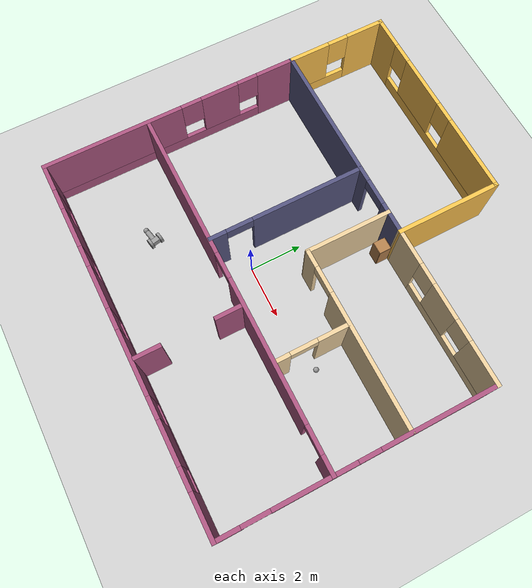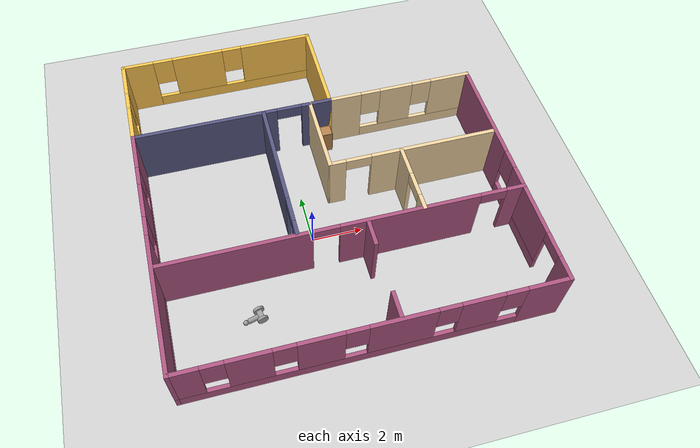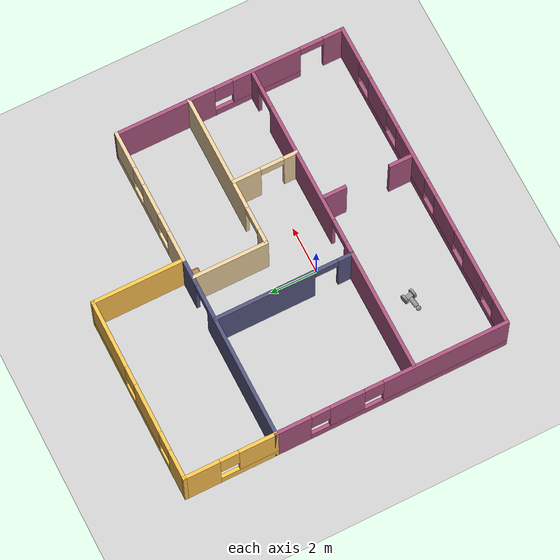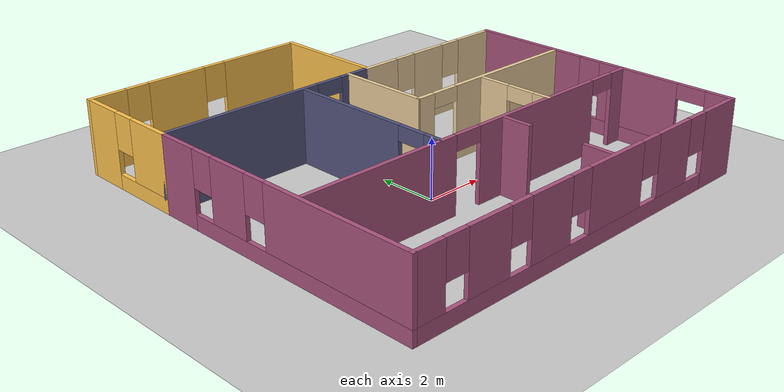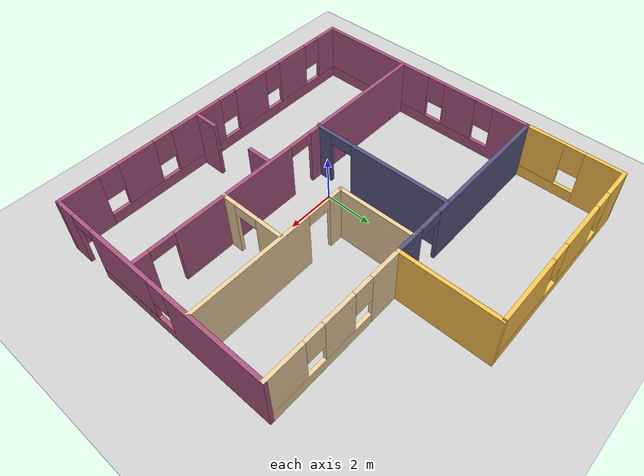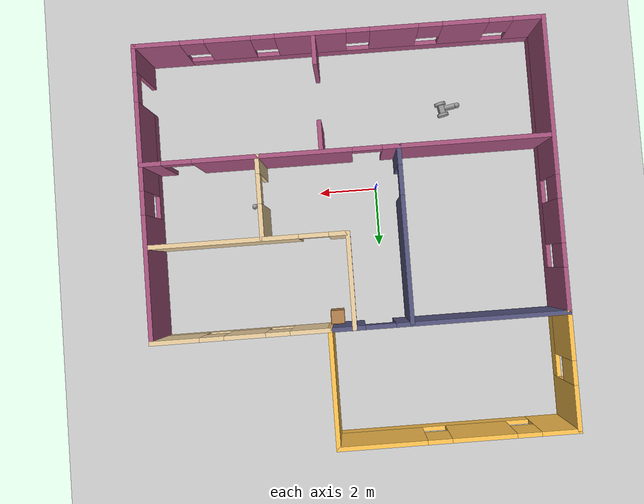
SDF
<sdf version="1.6">
 <world name="default">
  <plugin name="welcome" filename="libwelcome.so"/>
  <light name="sun" type="directional">
   <pose>0 0 10 0 -0 0</pose>
   <diffuse>0.8 0.8 0.8 1</diffuse>
   <specular>0.2 0.2 0.2 1</specular>
   <attenuation>
    <range>1000</range>
    <constant>0.9</constant>
    <linear>0.01</linear>
    <quadratic>0.001</quadratic>
   </attenuation>
   <direction>-0.5 0.1 -0.9</direction>
  </light>
  <model name="ground_plane">
   <static>1</static>
   <link name="link">
    <collision name="collision">
     <geometry><plane><normal>0 0 1</normal><size>100 100</size></plane></geometry>
     <surface>
      <contact><collide_bitmask>65535</collide_bitmask></contact>
      <friction><ode><mu>100</mu><mu2>50</mu2></ode></friction>
     </surface>
    </collision>
    <visual name="visual">
     <cast_shadows>0</cast_shadows>
     <geometry><plane><normal>0 0 1</normal><size>100 100</size></plane></geometry>
     <material>
      <script><uri>file://media/materials/scripts/gazebo.material</uri><name>Gazebo/Grey</name></script>
     </material>
    </visual>
   </link>
  </model>
  <gravity>0 0 -9.8</gravity>
  <magnetic_field>6e-06 2.3e-05 -4.2e-05</magnetic_field>
  <atmosphere type="adiabatic"/>
  <physics name="default_physics" default="0" type="ode">
   <max_step_size>0.001</max_step_size>
   <real_time_factor>1</real_time_factor>
   <real_time_update_rate>1000</real_time_update_rate>
  </physics>
  <scene><ambient>0.4 0.4 0.4 1</ambient><background>0.7 0.7 0.7 1</background><shadows>1</shadows></scene>
  <spherical_coordinates>
   <surface_model>EARTH_WGS84</surface_model>
   <latitude_deg>0</latitude_deg>
   <longitude_deg>0</longitude_deg>
   <elevation>0</elevation>
   <heading_deg>0</heading_deg>
  </spherical_coordinates>
  <model name="my_building">
   <pose>0.913 1.746 0 0 -0 0</pose>
   <link name="Wall_26">
    <pose>-2.925 6.85 0 0 -0 0</pose>
    <visual name="Wall_26_Visual_0">
     <pose>-3.34539 0 1.25 0 -0 0</pose>
     <geometry><box><size>1.30922 0.15 2.5</size></box></geometry>
     <material>
      <script><uri>file://media/materials/scripts/gazebo.material</uri><name>Gazebo/Grey</name></script>
      <ambient>1 0.764706 0.305882 1</ambient>
     </material>
     <meta><layer>0</layer></meta>
    </visual>
    <collision name="Wall_26_Collision_0">
     <geometry><box><size>1.30922 0.15 2.5</size></box></geometry>
     <pose>-3.34539 0 1.25 0 -0 0</pose>
    </collision>
    <visual name="Wall_26_Visual_1">
     <pose>0.654609 0 0.25 0 -0 0</pose>
     <geometry><box><size>6.69078 0.15 0.5</size></box></geometry>
     <material>
      <script><uri>file://media/materials/scripts/gazebo.material</uri><name>Gazebo/Grey</name></script>
      <ambient>1 0.764706 0.305882 1</ambient>
     </material>
     <meta><layer>0</layer></meta>
    </visual>
    <collision name="Wall_26_Collision_1">
     <geometry><box><size>6.69078 0.15 0.5</size></box></geometry>
     <pose>0.654609 0 0.25 0 -0 0</pose>
    </collision>
    <visual name="Wall_26_Visual_2">
     <pose>-0.835359 0 1.5 0 -0 0</pose>
     <geometry><box><size>2.11085 0.15 2</size></box></geometry>
     <material>
      <script><uri>file://media/materials/scripts/gazebo.material</uri><name>Gazebo/Grey</name></script>
      <ambient>1 0.764706 0.305882 1</ambient>
     </material>
     <meta><layer>0</layer></meta>
    </visual>
    <collision name="Wall_26_Collision_2">
     <geometry><box><size>2.11085 0.15 2</size></box></geometry>
     <pose>-0.835359 0 1.5 0 -0 0</pose>
    </collision>
    <visual name="Wall_26_Visual_3">
     <pose>2.51003 0 1.5 0 -0 0</pose>
     <geometry><box><size>2.97994 0.15 2</size></box></geometry>
     <material>
      <script><uri>file://media/materials/scripts/gazebo.material</uri><name>Gazebo/Grey</name></script>
      <ambient>1 0.764706 0.305882 1</ambient>
     </material>
     <meta><layer>0</layer></meta>
    </visual>
    <collision name="Wall_26_Collision_3">
     <geometry><box><size>2.97994 0.15 2</size></box></geometry>
     <pose>2.51003 0 1.5 0 -0 0</pose>
    </collision>
    <visual name="Wall_26_Visual_4">
     <pose>-2.29078 0 1.9 0 -0 0</pose>
     <geometry><box><size>0.8 0.15 1.2</size></box></geometry>
     <material>
      <script><uri>file://media/materials/scripts/gazebo.material</uri><name>Gazebo/Grey</name></script>
      <ambient>1 0.764706 0.305882 1</ambient>
     </material>
     <meta><layer>0</layer></meta>
    </visual>
    <collision name="Wall_26_Collision_4">
     <geometry><box><size>0.8 0.15 1.2</size></box></geometry>
     <pose>-2.29078 0 1.9 0 -0 0</pose>
    </collision>
    <visual name="Wall_26_Visual_5">
     <pose>0.620064 0 1.9 0 -0 0</pose>
     <geometry><box><size>0.8 0.15 1.2</size></box></geometry>
     <material>
      <script><uri>file://media/materials/scripts/gazebo.material</uri><name>Gazebo/Grey</name></script>
      <ambient>1 0.764706 0.305882 1</ambient>
     </material>
     <meta><layer>0</layer></meta>
    </visual>
    <collision name="Wall_26_Collision_5">
     <geometry><box><size>0.8 0.15 1.2</size></box></geometry>
     <pose>0.620064 0 1.9 0 -0 0</pose>
    </collision>
   </link>
   <link name="Wall_28">
    <collision name="Wall_28_Collision">
     <geometry><box><size>4 0.15 2.5</size></box></geometry>
     <pose>0 0 1.25 0 -0 0</pose>
    </collision>
    <visual name="Wall_28_Visual">
     <pose>0 0 1.25 0 -0 0</pose>
     <geometry><box><size>4 0.15 2.5</size></box></geometry>
     <material>
      <script><uri>file://media/materials/scripts/gazebo.material</uri><name>Gazebo/Grey</name></script>
      <ambient>1 0.764706 0.305882 1</ambient>
     </material>
     <meta><layer>0</layer></meta>
    </visual>
    <pose>1 4.925 0 0 0 -1.5708</pose>
   </link>
   <link name="Wall_30">
    <pose>3.925 3 0 0 -0 0</pose>
    <visual name="Wall_30_Visual_0">
     <pose>-2.30571 0 1.25 0 -0 0</pose>
     <geometry><box><size>1.38858 0.15 2.5</size></box></geometry>
     <material>
      <script><uri>file://media/materials/scripts/gazebo.material</uri><name>Gazebo/Grey</name></script>
      <ambient>0.921569 0.807843 0.615686 1</ambient>
     </material>
     <meta><layer>0</layer></meta>
    </visual>
    <collision name="Wall_30_Collision_0">
     <geometry><box><size>1.38858 0.15 2.5</size></box></geometry>
     <pose>-2.30571 0 1.25 0 -0 0</pose>
    </collision>
    <visual name="Wall_30_Visual_1">
     <pose>0.694289 0 0.25 0 -0 0</pose>
     <geometry><box><size>4.61142 0.15 0.5</size></box></geometry>
     <material>
      <script><uri>file://media/materials/scripts/gazebo.material</uri><name>Gazebo/Grey</name></script>
      <ambient>0.921569 0.807843 0.615686 1</ambient>
     </material>
     <meta><layer>0</layer></meta>
    </visual>
    <collision name="Wall_30_Collision_1">
     <geometry><box><size>4.61142 0.15 0.5</size></box></geometry>
     <pose>0.694289 0 0.25 0 -0 0</pose>
    </collision>
    <visual name="Wall_30_Visual_2">
     <pose>-0.130466 0 1.5 0 -0 0</pose>
     <geometry><box><size>1.36191 0.15 2</size></box></geometry>
     <material>
      <script><uri>file://media/materials/scripts/gazebo.material</uri><name>Gazebo/Grey</name></script>
      <ambient>0.921569 0.807843 0.615686 1</ambient>
     </material>
     <meta><layer>0</layer></meta>
    </visual>
    <collision name="Wall_30_Collision_2">
     <geometry><box><size>1.36191 0.15 2</size></box></geometry>
     <pose>-0.130466 0 1.5 0 -0 0</pose>
    </collision>
    <visual name="Wall_30_Visual_3">
     <pose>2.17524 0 1.5 0 -0 0</pose>
     <geometry><box><size>1.64951 0.15 2</size></box></geometry>
     <material>
      <script><uri>file://media/materials/scripts/gazebo.material</uri><name>Gazebo/Grey</name></script>
      <ambient>0.921569 0.807843 0.615686 1</ambient>
     </material>
     <meta><layer>0</layer></meta>
    </visual>
    <collision name="Wall_30_Collision_3">
     <geometry><box><size>1.64951 0.15 2</size></box></geometry>
     <pose>2.17524 0 1.5 0 -0 0</pose>
    </collision>
    <visual name="Wall_30_Visual_4">
     <pose>-1.21142 0 1.9 0 -0 0</pose>
     <geometry><box><size>0.8 0.15 1.2</size></box></geometry>
     <material>
      <script><uri>file://media/materials/scripts/gazebo.material</uri><name>Gazebo/Grey</name></script>
      <ambient>0.921569 0.807843 0.615686 1</ambient>
     </material>
     <meta><layer>0</layer></meta>
    </visual>
    <collision name="Wall_30_Collision_4">
     <geometry><box><size>0.8 0.15 1.2</size></box></geometry>
     <pose>-1.21142 0 1.9 0 -0 0</pose>
    </collision>
    <visual name="Wall_30_Visual_5">
     <pose>0.950489 0 1.9 0 -0 0</pose>
     <geometry><box><size>0.8 0.15 1.2</size></box></geometry>
     <material>
      <script><uri>file://media/materials/scripts/gazebo.material</uri><name>Gazebo/Grey</name></script>
      <ambient>0.921569 0.807843 0.615686 1</ambient>
     </material>
     <meta><layer>0</layer></meta>
    </visual>
    <collision name="Wall_30_Collision_5">
     <geometry><box><size>0.8 0.15 1.2</size></box></geometry>
     <pose>0.950489 0 1.9 0 -0 0</pose>
    </collision>
   </link>
   <link name="Wall_32">
    <pose>6.85 -1.925 0 0 0 -1.5708</pose>
    <visual name="Wall_32_Visual_0">
     <pose>-2.85473 0 1.25 0 -0 0</pose>
     <geometry><box><size>4.29055 0.15 2.5</size></box></geometry>
     <material>
      <script><uri>file://media/materials/scripts/gazebo.material</uri><name>Gazebo/Grey</name></script>
      <ambient>0.666667 0.333333 0.498039 1</ambient>
     </material>
     <meta><layer>0</layer></meta>
    </visual>
    <collision name="Wall_32_Collision_0">
     <geometry><box><size>4.29055 0.15 2.5</size></box></geometry>
     <pose>-2.85473 0 1.25 0 -0 0</pose>
    </collision>
    <visual name="Wall_32_Visual_1">
     <pose>4.52668 0 1.25 0 -0 0</pose>
     <geometry><box><size>0.94664 0.15 2.5</size></box></geometry>
     <material>
      <script><uri>file://media/materials/scripts/gazebo.material</uri><name>Gazebo/Grey</name></script>
      <ambient>0.666667 0.333333 0.498039 1</ambient>
     </material>
     <meta><layer>0</layer></meta>
    </visual>
    <collision name="Wall_32_Collision_1">
     <geometry><box><size>0.94664 0.15 2.5</size></box></geometry>
     <pose>4.52668 0 1.25 0 -0 0</pose>
    </collision>
    <visual name="Wall_32_Visual_2">
     <pose>1.17196 0 0.25 0 -0 0</pose>
     <geometry><box><size>3.76281 0.15 0.5</size></box></geometry>
     <material>
      <script><uri>file://media/materials/scripts/gazebo.material</uri><name>Gazebo/Grey</name></script>
      <ambient>0.666667 0.333333 0.498039 1</ambient>
     </material>
     <meta><layer>0</layer></meta>
    </visual>
    <collision name="Wall_32_Collision_2">
     <geometry><box><size>3.76281 0.15 0.5</size></box></geometry>
     <pose>1.17196 0 0.25 0 -0 0</pose>
    </collision>
    <visual name="Wall_32_Visual_3">
     <pose>1.57195 0 1.5 0 -0 0</pose>
     <geometry><box><size>2.96281 0.15 2</size></box></geometry>
     <material>
      <script><uri>file://media/materials/scripts/gazebo.material</uri><name>Gazebo/Grey</name></script>
      <ambient>0.666667 0.333333 0.498039 1</ambient>
     </material>
     <meta><layer>0</layer></meta>
    </visual>
    <collision name="Wall_32_Collision_3">
     <geometry><box><size>2.96281 0.15 2</size></box></geometry>
     <pose>1.57195 0 1.5 0 -0 0</pose>
    </collision>
    <visual name="Wall_32_Visual_4">
     <pose>-0.30945 0 1.9 0 -0 0</pose>
     <geometry><box><size>0.8 0.15 1.2</size></box></geometry>
     <material>
      <script><uri>file://media/materials/scripts/gazebo.material</uri><name>Gazebo/Grey</name></script>
      <ambient>0.666667 0.333333 0.498039 1</ambient>
     </material>
     <meta><layer>0</layer></meta>
    </visual>
    <collision name="Wall_32_Collision_4">
     <geometry><box><size>0.8 0.15 1.2</size></box></geometry>
     <pose>-0.30945 0 1.9 0 -0 0</pose>
    </collision>
    <visual name="Wall_32_Visual_5">
     <pose>3.55336 0 2.25 0 -0 0</pose>
     <geometry><box><size>1 0.15 0.5</size></box></geometry>
     <material>
      <script><uri>file://media/materials/scripts/gazebo.material</uri><name>Gazebo/Grey</name></script>
      <ambient>0.666667 0.333333 0.498039 1</ambient>
     </material>
     <meta><layer>0</layer></meta>
    </visual>
    <collision name="Wall_32_Collision_5">
     <geometry><box><size>1 0.15 0.5</size></box></geometry>
     <pose>3.55336 0 2.25 0 -0 0</pose>
    </collision>
   </link>
   <link name="Wall_35">
    <pose>-6.85 4.925 0 0 0 -1.5708</pose>
    <visual name="Wall_35_Visual_0">
     <pose>-1.22342 0 1.25 0 -0 0</pose>
     <geometry><box><size>1.55316 0.15 2.5</size></box></geometry>
     <material>
      <script><uri>file://media/materials/scripts/gazebo.material</uri><name>Gazebo/Grey</name></script>
      <ambient>1 0.764706 0.305882 1</ambient>
     </material>
     <meta><layer>0</layer></meta>
    </visual>
    <collision name="Wall_35_Collision_0">
     <geometry><box><size>1.55316 0.15 2.5</size></box></geometry>
     <pose>-1.22342 0 1.25 0 -0 0</pose>
    </collision>
    <visual name="Wall_35_Visual_1">
     <pose>0.77658 0 0.25 0 -0 0</pose>
     <geometry><box><size>2.44684 0.15 0.5</size></box></geometry>
     <material>
      <script><uri>file://media/materials/scripts/gazebo.material</uri><name>Gazebo/Grey</name></script>
      <ambient>1 0.764706 0.305882 1</ambient>
     </material>
     <meta><layer>0</layer></meta>
    </visual>
    <collision name="Wall_35_Collision_1">
     <geometry><box><size>2.44684 0.15 0.5</size></box></geometry>
     <pose>0.77658 0 0.25 0 -0 0</pose>
    </collision>
    <visual name="Wall_35_Visual_2">
     <pose>1.17658 0 1.5 0 -0 0</pose>
     <geometry><box><size>1.64684 0.15 2</size></box></geometry>
     <material>
      <script><uri>file://media/materials/scripts/gazebo.material</uri><name>Gazebo/Grey</name></script>
      <ambient>1 0.764706 0.305882 1</ambient>
     </material>
     <meta><layer>0</layer></meta>
    </visual>
    <collision name="Wall_35_Collision_2">
     <geometry><box><size>1.64684 0.15 2</size></box></geometry>
     <pose>1.17658 0 1.5 0 -0 0</pose>
    </collision>
    <visual name="Wall_35_Visual_3">
     <pose>-0.046841 0 1.9 0 -0 0</pose>
     <geometry><box><size>0.8 0.15 1.2</size></box></geometry>
     <material>
      <script><uri>file://media/materials/scripts/gazebo.material</uri><name>Gazebo/Grey</name></script>
      <ambient>1 0.764706 0.305882 1</ambient>
     </material>
     <meta><layer>0</layer></meta>
    </visual>
    <collision name="Wall_35_Collision_3">
     <geometry><box><size>0.8 0.15 1.2</size></box></geometry>
     <pose>-0.046841 0 1.9 0 -0 0</pose>
    </collision>
   </link>
   <link name="Wall_37">
    <pose>-2.925 3 0 0 -0 0</pose>
    <visual name="Wall_37_Visual_0">
     <pose>-1.1232 0 1.25 0 -0 0</pose>
     <geometry><box><size>5.75361 0.15 2.5</size></box></geometry>
     <material>
      <script><uri>file://media/materials/scripts/gazebo.material</uri><name>Gazebo/Grey</name></script>
      <ambient>0.333333 0.333333 0.498039 1</ambient>
     </material>
     <meta><layer>0</layer></meta>
    </visual>
    <collision name="Wall_37_Collision_0">
     <geometry><box><size>5.75361 0.15 2.5</size></box></geometry>
     <pose>-1.1232 0 1.25 0 -0 0</pose>
    </collision>
    <visual name="Wall_37_Visual_1">
     <pose>3.3768 0 1.25 0 -0 0</pose>
     <geometry><box><size>1.24639 0.15 2.5</size></box></geometry>
     <material>
      <script><uri>file://media/materials/scripts/gazebo.material</uri><name>Gazebo/Grey</name></script>
      <ambient>0.333333 0.333333 0.498039 1</ambient>
     </material>
     <meta><layer>0</layer></meta>
    </visual>
    <collision name="Wall_37_Collision_1">
     <geometry><box><size>1.24639 0.15 2.5</size></box></geometry>
     <pose>3.3768 0 1.25 0 -0 0</pose>
    </collision>
    <visual name="Wall_37_Visual_2">
     <pose>2.2536 0 2.25 0 -0 0</pose>
     <geometry><box><size>1 0.15 0.5</size></box></geometry>
     <material>
      <script><uri>file://media/materials/scripts/gazebo.material</uri><name>Gazebo/Grey</name></script>
      <ambient>0.333333 0.333333 0.498039 1</ambient>
     </material>
     <meta><layer>0</layer></meta>
    </visual>
    <collision name="Wall_37_Collision_2">
     <geometry><box><size>1 0.15 0.5</size></box></geometry>
     <pose>2.2536 0 2.25 0 -0 0</pose>
    </collision>
   </link>
   <link name="Wall_39">
    <pose>-6.85 -1.925 0 0 0 -1.5708</pose>
    <visual name="Wall_39_Visual_0">
     <pose>-4.22364 0 1.25 0 -0 0</pose>
     <geometry><box><size>1.55272 0.15 2.5</size></box></geometry>
     <material>
      <script><uri>file://media/materials/scripts/gazebo.material</uri><name>Gazebo/Grey</name></script>
      <ambient>0.666667 0.333333 0.498039 1</ambient>
     </material>
     <meta><layer>0</layer></meta>
    </visual>
    <collision name="Wall_39_Collision_0">
     <geometry><box><size>1.55272 0.15 2.5</size></box></geometry>
     <pose>-4.22364 0 1.25 0 -0 0</pose>
    </collision>
    <visual name="Wall_39_Visual_1">
     <pose>0.776358 0 0.25 0 -0 0</pose>
     <geometry><box><size>8.44728 0.15 0.5</size></box></geometry>
     <material>
      <script><uri>file://media/materials/scripts/gazebo.material</uri><name>Gazebo/Grey</name></script>
      <ambient>0.666667 0.333333 0.498039 1</ambient>
     </material>
     <meta><layer>0</layer></meta>
    </visual>
    <collision name="Wall_39_Collision_1">
     <geometry><box><size>8.44728 0.15 0.5</size></box></geometry>
     <pose>0.776358 0 0.25 0 -0 0</pose>
    </collision>
    <visual name="Wall_39_Visual_2">
     <pose>-1.91089 0 1.5 0 -0 0</pose>
     <geometry><box><size>1.47279 0.15 2</size></box></geometry>
     <material>
      <script><uri>file://media/materials/scripts/gazebo.material</uri><name>Gazebo/Grey</name></script>
      <ambient>0.666667 0.333333 0.498039 1</ambient>
     </material>
     <meta><layer>0</layer></meta>
    </visual>
    <collision name="Wall_39_Collision_2">
     <geometry><box><size>1.47279 0.15 2</size></box></geometry>
     <pose>-1.91089 0 1.5 0 -0 0</pose>
    </collision>
    <visual name="Wall_39_Visual_3">
     <pose>2.31275 0 1.5 0 -0 0</pose>
     <geometry><box><size>5.37449 0.15 2</size></box></geometry>
     <material>
      <script><uri>file://media/materials/scripts/gazebo.material</uri><name>Gazebo/Grey</name></script>
      <ambient>0.666667 0.333333 0.498039 1</ambient>
     </material>
     <meta><layer>0</layer></meta>
    </visual>
    <collision name="Wall_39_Collision_3">
     <geometry><box><size>5.37449 0.15 2</size></box></geometry>
     <pose>2.31275 0 1.5 0 -0 0</pose>
    </collision>
    <visual name="Wall_39_Visual_4">
     <pose>-3.04728 0 1.9 0 -0 0</pose>
     <geometry><box><size>0.8 0.15 1.2</size></box></geometry>
     <material>
      <script><uri>file://media/materials/scripts/gazebo.material</uri><name>Gazebo/Grey</name></script>
      <ambient>0.666667 0.333333 0.498039 1</ambient>
     </material>
     <meta><layer>0</layer></meta>
    </visual>
    <collision name="Wall_39_Collision_4">
     <geometry><box><size>0.8 0.15 1.2</size></box></geometry>
     <pose>-3.04728 0 1.9 0 -0 0</pose>
    </collision>
    <visual name="Wall_39_Visual_5">
     <pose>-0.774493 0 1.9 0 -0 0</pose>
     <geometry><box><size>0.8 0.15 1.2</size></box></geometry>
     <material>
      <script><uri>file://media/materials/scripts/gazebo.material</uri><name>Gazebo/Grey</name></script>
      <ambient>0.666667 0.333333 0.498039 1</ambient>
     </material>
     <meta><layer>0</layer></meta>
    </visual>
    <collision name="Wall_39_Collision_5">
     <geometry><box><size>0.8 0.15 1.2</size></box></geometry>
     <pose>-0.774493 0 1.9 0 -0 0</pose>
    </collision>
   </link>
   <link name="Wall_41">
    <pose>0 -6.85 0 0 -0 3.14159</pose>
    <visual name="Wall_41_Visual_0">
     <pose>-6.11101 0 1.25 0 -0 0</pose>
     <geometry><box><size>1.62797 0.15 2.5</size></box></geometry>
     <material>
      <script><uri>file://media/materials/scripts/gazebo.material</uri><name>Gazebo/Grey</name></script>
      <ambient>0.666667 0.333333 0.498039 1</ambient>
     </material>
     <meta><layer>0</layer></meta>
    </visual>
    <collision name="Wall_41_Collision_0">
     <geometry><box><size>1.62797 0.15 2.5</size></box></geometry>
     <pose>-6.11101 0 1.25 0 -0 0</pose>
    </collision>
    <visual name="Wall_41_Visual_1">
     <pose>0.813987 0 0.25 0 -0 0</pose>
     <geometry><box><size>12.222 0.15 0.5</size></box></geometry>
     <material>
      <script><uri>file://media/materials/scripts/gazebo.material</uri><name>Gazebo/Grey</name></script>
      <ambient>0.666667 0.333333 0.498039 1</ambient>
     </material>
     <meta><layer>0</layer></meta>
    </visual>
    <collision name="Wall_41_Collision_1">
     <geometry><box><size>12.222 0.15 0.5</size></box></geometry>
     <pose>0.813987 0 0.25 0 -0 0</pose>
    </collision>
    <visual name="Wall_41_Visual_2">
     <pose>-3.72076 0 1.5 0 -0 0</pose>
     <geometry><box><size>1.55254 0.15 2</size></box></geometry>
     <material>
      <script><uri>file://media/materials/scripts/gazebo.material</uri><name>Gazebo/Grey</name></script>
      <ambient>0.666667 0.333333 0.498039 1</ambient>
     </material>
     <meta><layer>0</layer></meta>
    </visual>
    <collision name="Wall_41_Collision_2">
     <geometry><box><size>1.55254 0.15 2</size></box></geometry>
     <pose>-3.72076 0 1.5 0 -0 0</pose>
    </collision>
    <visual name="Wall_41_Visual_3">
     <pose>-0.949548 0 1.5 0 -0 0</pose>
     <geometry><box><size>2.38988 0.15 2</size></box></geometry>
     <material>
      <script><uri>file://media/materials/scripts/gazebo.material</uri><name>Gazebo/Grey</name></script>
      <ambient>0.666667 0.333333 0.498039 1</ambient>
     </material>
     <meta><layer>0</layer></meta>
    </visual>
    <collision name="Wall_41_Collision_3">
     <geometry><box><size>2.38988 0.15 2</size></box></geometry>
     <pose>-0.949548 0 1.5 0 -0 0</pose>
    </collision>
    <visual name="Wall_41_Visual_4">
     <pose>1.86154 0 1.5 0 -0 0</pose>
     <geometry><box><size>1.63228 0.15 2</size></box></geometry>
     <material>
      <script><uri>file://media/materials/scripts/gazebo.material</uri><name>Gazebo/Grey</name></script>
      <ambient>0.666667 0.333333 0.498039 1</ambient>
     </material>
     <meta><layer>0</layer></meta>
    </visual>
    <collision name="Wall_41_Collision_4">
     <geometry><box><size>1.63228 0.15 2</size></box></geometry>
     <pose>1.86154 0 1.5 0 -0 0</pose>
    </collision>
    <visual name="Wall_41_Visual_5">
     <pose>4.25395 0 1.5 0 -0 0</pose>
     <geometry><box><size>1.55254 0.15 2</size></box></geometry>
     <material>
      <script><uri>file://media/materials/scripts/gazebo.material</uri><name>Gazebo/Grey</name></script>
      <ambient>0.666667 0.333333 0.498039 1</ambient>
     </material>
     <meta><layer>0</layer></meta>
    </visual>
    <collision name="Wall_41_Collision_5">
     <geometry><box><size>1.55254 0.15 2</size></box></geometry>
     <pose>4.25395 0 1.5 0 -0 0</pose>
    </collision>
    <visual name="Wall_41_Visual_6">
     <pose>6.37761 0 1.5 0 -0 0</pose>
     <geometry><box><size>1.09478 0.15 2</size></box></geometry>
     <material>
      <script><uri>file://media/materials/scripts/gazebo.material</uri><name>Gazebo/Grey</name></script>
      <ambient>0.666667 0.333333 0.498039 1</ambient>
     </material>
     <meta><layer>0</layer></meta>
    </visual>
    <collision name="Wall_41_Collision_6">
     <geometry><box><size>1.09478 0.15 2</size></box></geometry>
     <pose>6.37761 0 1.5 0 -0 0</pose>
    </collision>
    <visual name="Wall_41_Visual_7">
     <pose>-4.89703 0 1.9 0 -0 0</pose>
     <geometry><box><size>0.8 0.15 1.2</size></box></geometry>
     <material>
      <script><uri>file://media/materials/scripts/gazebo.material</uri><name>Gazebo/Grey</name></script>
      <ambient>0.666667 0.333333 0.498039 1</ambient>
     </material>
     <meta><layer>0</layer></meta>
    </visual>
    <collision name="Wall_41_Collision_7">
     <geometry><box><size>0.8 0.15 1.2</size></box></geometry>
     <pose>-4.89703 0 1.9 0 -0 0</pose>
    </collision>
    <visual name="Wall_41_Visual_8">
     <pose>-2.54449 0 1.9 0 -0 0</pose>
     <geometry><box><size>0.8 0.15 1.2</size></box></geometry>
     <material>
      <script><uri>file://media/materials/scripts/gazebo.material</uri><name>Gazebo/Grey</name></script>
      <ambient>0.666667 0.333333 0.498039 1</ambient>
     </material>
     <meta><layer>0</layer></meta>
    </visual>
    <collision name="Wall_41_Collision_8">
     <geometry><box><size>0.8 0.15 1.2</size></box></geometry>
     <pose>-2.54449 0 1.9 0 -0 0</pose>
    </collision>
    <visual name="Wall_41_Visual_9">
     <pose>0.645393 0 1.9 0 -0 0</pose>
     <geometry><box><size>0.8 0.15 1.2</size></box></geometry>
     <material>
      <script><uri>file://media/materials/scripts/gazebo.material</uri><name>Gazebo/Grey</name></script>
      <ambient>0.666667 0.333333 0.498039 1</ambient>
     </material>
     <meta><layer>0</layer></meta>
    </visual>
    <collision name="Wall_41_Collision_9">
     <geometry><box><size>0.8 0.15 1.2</size></box></geometry>
     <pose>0.645393 0 1.9 0 -0 0</pose>
    </collision>
    <visual name="Wall_41_Visual_10">
     <pose>3.07768 0 1.9 0 -0 0</pose>
     <geometry><box><size>0.8 0.15 1.2</size></box></geometry>
     <material>
      <script><uri>file://media/materials/scripts/gazebo.material</uri><name>Gazebo/Grey</name></script>
      <ambient>0.666667 0.333333 0.498039 1</ambient>
     </material>
     <meta><layer>0</layer></meta>
    </visual>
    <collision name="Wall_41_Collision_10">
     <geometry><box><size>0.8 0.15 1.2</size></box></geometry>
     <pose>3.07768 0 1.9 0 -0 0</pose>
    </collision>
    <visual name="Wall_41_Visual_11">
     <pose>5.43022 0 1.9 0 -0 0</pose>
     <geometry><box><size>0.8 0.15 1.2</size></box></geometry>
     <material>
      <script><uri>file://media/materials/scripts/gazebo.material</uri><name>Gazebo/Grey</name></script>
      <ambient>0.666667 0.333333 0.498039 1</ambient>
     </material>
     <meta><layer>0</layer></meta>
    </visual>
    <collision name="Wall_41_Collision_11">
     <geometry><box><size>0.8 0.15 1.2</size></box></geometry>
     <pose>5.43022 0 1.9 0 -0 0</pose>
    </collision>
   </link>
   <link name="Wall_44">
    <pose>0.043501 -2.87666 0 0 -0 0</pose>
    <visual name="Wall_44_Visual_0">
     <pose>-4.04041 0 1.25 0 -0 0</pose>
     <geometry><box><size>5.66919 0.15 2.5</size></box></geometry>
     <material>
      <script><uri>file://media/materials/scripts/gazebo.material</uri><name>Gazebo/Grey</name></script>
      <ambient>0.666667 0.333333 0.498039 1</ambient>
     </material>
     <meta><layer>0</layer></meta>
    </visual>
    <collision name="Wall_44_Collision_0">
     <geometry><box><size>5.66919 0.15 2.5</size></box></geometry>
     <pose>-4.04041 0 1.25 0 -0 0</pose>
    </collision>
    <visual name="Wall_44_Visual_1">
     <pose>2.45815 0 1.25 0 -0 0</pose>
     <geometry><box><size>5.32793 0.15 2.5</size></box></geometry>
     <material>
      <script><uri>file://media/materials/scripts/gazebo.material</uri><name>Gazebo/Grey</name></script>
      <ambient>0.666667 0.333333 0.498039 1</ambient>
     </material>
     <meta><layer>0</layer></meta>
    </visual>
    <collision name="Wall_44_Collision_1">
     <geometry><box><size>5.32793 0.15 2.5</size></box></geometry>
     <pose>2.45815 0 1.25 0 -0 0</pose>
    </collision>
    <visual name="Wall_44_Visual_2">
     <pose>6.49856 0 1.25 0 -0 0</pose>
     <geometry><box><size>0.752884 0.15 2.5</size></box></geometry>
     <material>
      <script><uri>file://media/materials/scripts/gazebo.material</uri><name>Gazebo/Grey</name></script>
      <ambient>0.666667 0.333333 0.498039 1</ambient>
     </material>
     <meta><layer>0</layer></meta>
    </visual>
    <collision name="Wall_44_Collision_2">
     <geometry><box><size>0.752884 0.15 2.5</size></box></geometry>
     <pose>6.49856 0 1.25 0 -0 0</pose>
    </collision>
    <visual name="Wall_44_Visual_3">
     <pose>-0.705812 0 2.25 0 -0 0</pose>
     <geometry><box><size>1 0.15 0.5</size></box></geometry>
     <material>
      <script><uri>file://media/materials/scripts/gazebo.material</uri><name>Gazebo/Grey</name></script>
      <ambient>0.666667 0.333333 0.498039 1</ambient>
     </material>
     <meta><layer>0</layer></meta>
    </visual>
    <collision name="Wall_44_Collision_3">
     <geometry><box><size>1 0.15 0.5</size></box></geometry>
     <pose>-0.705812 0 2.25 0 -0 0</pose>
    </collision>
    <visual name="Wall_44_Visual_4">
     <pose>5.62212 0 2.25 0 -0 0</pose>
     <geometry><box><size>1 0.15 0.5</size></box></geometry>
     <material>
      <script><uri>file://media/materials/scripts/gazebo.material</uri><name>Gazebo/Grey</name></script>
      <ambient>0.666667 0.333333 0.498039 1</ambient>
     </material>
     <meta><layer>0</layer></meta>
    </visual>
    <collision name="Wall_44_Collision_4">
     <geometry><box><size>1 0.15 0.5</size></box></geometry>
     <pose>5.62212 0 2.25 0 -0 0</pose>
    </collision>
   </link>
   <link name="Wall_47">
    <collision name="Wall_47_Collision">
     <geometry><box><size>3.27 0.15 2.5</size></box></geometry>
     <pose>0 0 1.25 0 -0 0</pose>
    </collision>
    <visual name="Wall_47_Visual">
     <pose>0 0 1.25 0 -0 0</pose>
     <geometry><box><size>3.27 0.15 2.5</size></box></geometry>
     <material>
      <script><uri>file://media/materials/scripts/gazebo.material</uri><name>Gazebo/Grey</name></script>
      <ambient>0.921569 0.807843 0.615686 1</ambient>
     </material>
     <meta><layer>0</layer></meta>
    </visual>
    <pose>0.189 1.43 0 0 0 -1.5708</pose>
   </link>
   <link name="Wall_49">
    <pose>-1.705 0.0515 0 0 0 -1.5708</pose>
    <visual name="Wall_49_Visual_0">
     <pose>-0.836875 0 1.25 0 -0 0</pose>
     <geometry><box><size>4.27125 0.15 2.5</size></box></geometry>
     <material>
      <script><uri>file://media/materials/scripts/gazebo.material</uri><name>Gazebo/Grey</name></script>
      <ambient>0.333333 0.333333 0.498039 1</ambient>
     </material>
     <meta><layer>0</layer></meta>
    </visual>
    <collision name="Wall_49_Collision_0">
     <geometry><box><size>4.27125 0.15 2.5</size></box></geometry>
     <pose>-0.836875 0 1.25 0 -0 0</pose>
    </collision>
    <visual name="Wall_49_Visual_1">
     <pose>2.63563 0 1.25 0 -0 0</pose>
     <geometry><box><size>0.67375 0.15 2.5</size></box></geometry>
     <material>
      <script><uri>file://media/materials/scripts/gazebo.material</uri><name>Gazebo/Grey</name></script>
      <ambient>0.333333 0.333333 0.498039 1</ambient>
     </material>
     <meta><layer>0</layer></meta>
    </visual>
    <collision name="Wall_49_Collision_1">
     <geometry><box><size>0.67375 0.15 2.5</size></box></geometry>
     <pose>2.63563 0 1.25 0 -0 0</pose>
    </collision>
    <visual name="Wall_49_Visual_2">
     <pose>1.79875 0 2.25 0 -0 0</pose>
     <geometry><box><size>1 0.15 0.5</size></box></geometry>
     <material>
      <script><uri>file://media/materials/scripts/gazebo.material</uri><name>Gazebo/Grey</name></script>
      <ambient>0.333333 0.333333 0.498039 1</ambient>
     </material>
     <meta><layer>0</layer></meta>
    </visual>
    <collision name="Wall_49_Collision_2">
     <geometry><box><size>1 0.15 0.5</size></box></geometry>
     <pose>1.79875 0 2.25 0 -0 0</pose>
    </collision>
   </link>
   <link name="Wall_51">
    <pose>3.53653 -0.137125 0 0 -0 0</pose>
    <visual name="Wall_51_Visual_0">
     <pose>-3.04888 0 1.25 0 -0 0</pose>
     <geometry><box><size>0.652229 0.15 2.5</size></box></geometry>
     <material>
      <script><uri>file://media/materials/scripts/gazebo.material</uri><name>Gazebo/Grey</name></script>
      <ambient>0.921569 0.807843 0.615686 1</ambient>
     </material>
     <meta><layer>0</layer></meta>
    </visual>
    <collision name="Wall_51_Collision_0">
     <geometry><box><size>0.652229 0.15 2.5</size></box></geometry>
     <pose>-3.04888 0 1.25 0 -0 0</pose>
    </collision>
    <visual name="Wall_51_Visual_1">
     <pose>0.826115 0 1.25 0 -0 0</pose>
     <geometry><box><size>5.09777 0.15 2.5</size></box></geometry>
     <material>
      <script><uri>file://media/materials/scripts/gazebo.material</uri><name>Gazebo/Grey</name></script>
      <ambient>0.921569 0.807843 0.615686 1</ambient>
     </material>
     <meta><layer>0</layer></meta>
    </visual>
    <collision name="Wall_51_Collision_1">
     <geometry><box><size>5.09777 0.15 2.5</size></box></geometry>
     <pose>0.826115 0 1.25 0 -0 0</pose>
    </collision>
    <visual name="Wall_51_Visual_2">
     <pose>-2.22277 0 2.25 0 -0 0</pose>
     <geometry><box><size>1 0.15 0.5</size></box></geometry>
     <material>
      <script><uri>file://media/materials/scripts/gazebo.material</uri><name>Gazebo/Grey</name></script>
      <ambient>0.921569 0.807843 0.615686 1</ambient>
     </material>
     <meta><layer>0</layer></meta>
    </visual>
    <collision name="Wall_51_Collision_2">
     <geometry><box><size>1 0.15 0.5</size></box></geometry>
     <pose>-2.22277 0 2.25 0 -0 0</pose>
    </collision>
   </link>
   <link name="Wall_53">
    <pose>3.01 -1.5185 0 0 0 -1.5708</pose>
    <visual name="Wall_53_Visual_0">
     <pose>-0.823687 0 1.25 0 -0 0</pose>
     <geometry><box><size>1.21763 0.15 2.5</size></box></geometry>
     <material>
      <script><uri>file://media/materials/scripts/gazebo.material</uri><name>Gazebo/Grey</name></script>
      <ambient>0.921569 0.807843 0.615686 1</ambient>
     </material>
     <meta><layer>0</layer></meta>
    </visual>
    <collision name="Wall_53_Collision_0">
     <geometry><box><size>1.21763 0.15 2.5</size></box></geometry>
     <pose>-0.823687 0 1.25 0 -0 0</pose>
    </collision>
    <visual name="Wall_53_Visual_1">
     <pose>1.10881 0 1.25 0 -0 0</pose>
     <geometry><box><size>0.647374 0.15 2.5</size></box></geometry>
     <material>
      <script><uri>file://media/materials/scripts/gazebo.material</uri><name>Gazebo/Grey</name></script>
      <ambient>0.921569 0.807843 0.615686 1</ambient>
     </material>
     <meta><layer>0</layer></meta>
    </visual>
    <collision name="Wall_53_Collision_1">
     <geometry><box><size>0.647374 0.15 2.5</size></box></geometry>
     <pose>1.10881 0 1.25 0 -0 0</pose>
    </collision>
    <visual name="Wall_53_Visual_2">
     <pose>0.285126 0 2.25 0 -0 0</pose>
     <geometry><box><size>1 0.15 0.5</size></box></geometry>
     <material>
      <script><uri>file://media/materials/scripts/gazebo.material</uri><name>Gazebo/Grey</name></script>
      <ambient>0.921569 0.807843 0.615686 1</ambient>
     </material>
     <meta><layer>0</layer></meta>
    </visual>
    <collision name="Wall_53_Collision_2">
     <geometry><box><size>1 0.15 0.5</size></box></geometry>
     <pose>0.285126 0 2.25 0 -0 0</pose>
    </collision>
   </link>
   <link name="Wall_57">
    <collision name="Wall_57_Collision">
     <geometry><box><size>1 0.15 2.5</size></box></geometry>
     <pose>0 0 1.25 0 -0 0</pose>
    </collision>
    <visual name="Wall_57_Visual">
     <pose>0 0 1.25 0 -0 0</pose>
     <geometry><box><size>1 0.15 2.5</size></box></geometry>
     <material>
      <script><uri>file://media/materials/scripts/gazebo.material</uri><name>Gazebo/Grey</name></script>
      <ambient>0.666667 0.333333 0.498039 1</ambient>
     </material>
     <meta><layer>0</layer></meta>
    </visual>
    <pose>0.865 -6.3 0 0 -0 1.5708</pose>
   </link>
   <link name="Wall_61">
    <collision name="Wall_61_Collision">
     <geometry><box><size>1 0.15 2.5</size></box></geometry>
     <pose>0 0 1.25 0 -0 0</pose>
    </collision>
    <visual name="Wall_61_Visual">
     <pose>0 0 1.25 0 -0 0</pose>
     <geometry><box><size>1 0.15 2.5</size></box></geometry>
     <material>
      <script><uri>file://media/materials/scripts/gazebo.material</uri><name>Gazebo/Grey</name></script>
      <ambient>0.666667 0.333333 0.498039 1</ambient>
     </material>
     <meta><layer>0</layer></meta>
    </visual>
    <pose>0.867 -3.43606 0 0 0 -1.5708</pose>
   </link>
   <static>1</static>
  </model>
  <model name="myrobot">
   <link name="link_0">
    <pose>-2.80219 -2.70394 0.2 0 -0 0</pose>
    <inertial>
     <mass>1</mass>
     <inertia>
      <ixx>0.166667</ixx>
      <ixy>0</ixy>
      <ixz>0</ixz>
      <iyy>0.166667</iyy>
      <iyz>0</iyz>
      <izz>0.166667</izz>
     </inertia>
    </inertial>
    <visual name="visual">
     <geometry><box><size>0.2 0.3 0.2</size></box></geometry>
     <material>
      <lighting>1</lighting>
      <script><uri>file://media/materials/scripts/gazebo.material</uri><name>Gazebo/Grey</name></script>
      <shader type="pixel"><normal_map>__default__</normal_map></shader>
      <ambient>0.3 0.3 0.3 1</ambient>
      <diffuse>0.7 0.7 0.7 1</diffuse>
      <specular>0.01 0.01 0.01 1</specular>
      <emissive>0 0 0 1</emissive>
     </material>
    </visual>
    <collision name="collision">
     <geometry><box><size>0.2 0.3 0.2</size></box></geometry>
     <surface>
      <friction>
       <ode><mu>1</mu><mu2>1</mu2><fdir1>0 0 0</fdir1><slip1>0</slip1><slip2>0</slip2></ode>
       <torsional>
        <coefficient>1</coefficient>
        <patch_radius>0</patch_radius>
        <surface_radius>0</surface_radius>
        <use_patch_radius>1</use_patch_radius>
        <ode><slip>0</slip></ode>
       </torsional>
      </friction>
      <bounce><restitution_coefficient>0</restitution_coefficient><threshold>1e+06</threshold></bounce>
      <contact>
       <collide_without_contact>0</collide_without_contact>
       <collide_without_contact_bitmask>1</collide_without_contact_bitmask>
       <collide_bitmask>1</collide_bitmask>
       <ode>
        <soft_cfm>0</soft_cfm>
        <soft_erp>0.2</soft_erp>
        <kp>1e+13</kp>
        <kd>1</kd>
        <max_vel>0.01</max_vel>
        <min_depth>0</min_depth>
       </ode>
       <bullet>
        <split_impulse>1</split_impulse>
        <split_impulse_penetration_threshold>-0.01</split_impulse_penetration_threshold>
        <soft_cfm>0</soft_cfm>
        <soft_erp>0.2</soft_erp>
        <kp>1e+13</kp>
        <kd>1</kd>
       </bullet>
      </contact>
     </surface>
    </collision>
   </link>
   <link name="link_0_clone">
    <pose>-3.32477 -3.96593 0.2 0 -0 0</pose>
    <inertial>
     <mass>1</mass>
     <inertia>
      <ixx>0.166667</ixx>
      <ixy>0</ixy>
      <ixz>0</ixz>
      <iyy>0.166667</iyy>
      <iyz>0</iyz>
      <izz>0.166667</izz>
     </inertia>
    </inertial>
    <visual name="visual">
     <geometry><box><size>0.2 0.3 0.2</size></box></geometry>
     <material>
      <lighting>1</lighting>
      <script><uri>file://media/materials/scripts/gazebo.material</uri><name>Gazebo/Grey</name></script>
      <shader type="pixel"><normal_map>__default__</normal_map></shader>
      <ambient>0.3 0.3 0.3 1</ambient>
      <diffuse>0.7 0.7 0.7 1</diffuse>
      <specular>0.01 0.01 0.01 1</specular>
      <emissive>0 0 0 1</emissive>
     </material>
    </visual>
    <collision name="collision">
     <geometry><box><size>0.2 0.3 0.2</size></box></geometry>
     <surface>
      <friction>
       <ode><mu>1</mu><mu2>1</mu2><fdir1>0 0 0</fdir1><slip1>0</slip1><slip2>0</slip2></ode>
       <torsional>
        <coefficient>1</coefficient>
        <patch_radius>0</patch_radius>
        <surface_radius>0</surface_radius>
        <use_patch_radius>1</use_patch_radius>
        <ode><slip>0</slip></ode>
       </torsional>
      </friction>
      <bounce><restitution_coefficient>0</restitution_coefficient><threshold>1e+06</threshold></bounce>
      <contact>
       <collide_without_contact>0</collide_without_contact>
       <collide_without_contact_bitmask>1</collide_without_contact_bitmask>
       <collide_bitmask>1</collide_bitmask>
       <ode>
        <soft_cfm>0</soft_cfm>
        <soft_erp>0.2</soft_erp>
        <kp>1e+13</kp>
        <kd>1</kd>
        <max_vel>0.01</max_vel>
        <min_depth>0</min_depth>
       </ode>
       <bullet>
        <split_impulse>1</split_impulse>
        <split_impulse_penetration_threshold>-0.01</split_impulse_penetration_threshold>
        <soft_cfm>0</soft_cfm>
        <soft_erp>0.2</soft_erp>
        <kp>1e+13</kp>
        <kd>1</kd>
       </bullet>
      </contact>
     </surface>
    </collision>
   </link>
   <link name="link_1">
    <pose>-2.78219 -2.90396 0.2 1.5707 -0 0</pose>
    <inertial>
     <mass>1</mass>
     <inertia><ixx>0.145833</ixx><ixy>0</ixy><ixz>0</ixz><iyy>0.145833</iyy><iyz>0</iyz><izz>0.125</izz></inertia>
    </inertial>
    <visual name="visual">
     <geometry><cylinder><radius>0.2</radius><length>0.1</length></cylinder></geometry>
     <material>
      <lighting>1</lighting>
      <script><uri>file://media/materials/scripts/gazebo.material</uri><name>Gazebo/Grey</name></script>
      <shader type="pixel"><normal_map>__default__</normal_map></shader>
      <ambient>0.3 0.3 0.3 1</ambient>
      <diffuse>0.7 0.7 0.7 1</diffuse>
      <specular>0.01 0.01 0.01 1</specular>
      <emissive>0 0 0 1</emissive>
     </material>
    </visual>
    <collision name="collision">
     <geometry><cylinder><radius>0.2</radius><length>0.1</length></cylinder></geometry>
     <surface>
      <friction>
       <ode><mu>1</mu><mu2>1</mu2><fdir1>0 0 0</fdir1><slip1>0</slip1><slip2>0</slip2></ode>
       <torsional>
        <coefficient>1</coefficient>
        <patch_radius>0</patch_radius>
        <surface_radius>0</surface_radius>
        <use_patch_radius>1</use_patch_radius>
        <ode><slip>0</slip></ode>
       </torsional>
      </friction>
      <bounce><restitution_coefficient>0</restitution_coefficient><threshold>1e+06</threshold></bounce>
      <contact>
       <collide_without_contact>0</collide_without_contact>
       <collide_without_contact_bitmask>1</collide_without_contact_bitmask>
       <collide_bitmask>1</collide_bitmask>
       <ode>
        <soft_cfm>0</soft_cfm>
        <soft_erp>0.2</soft_erp>
        <kp>1e+13</kp>
        <kd>1</kd>
        <max_vel>0.01</max_vel>
        <min_depth>0</min_depth>
       </ode>
       <bullet>
        <split_impulse>1</split_impulse>
        <split_impulse_penetration_threshold>-0.01</split_impulse_penetration_threshold>
        <soft_cfm>0</soft_cfm>
        <soft_erp>0.2</soft_erp>
        <kp>1e+13</kp>
        <kd>1</kd>
       </bullet>
      </contact>
     </surface>
    </collision>
   </link>
   <link name="link_1_clone">
    <pose>-2.78219 -2.50392 0.2 1.5707 -0 0</pose>
    <inertial>
     <mass>1</mass>
     <inertia><ixx>0.145833</ixx><ixy>0</ixy><ixz>0</ixz><iyy>0.145833</iyy><iyz>0</iyz><izz>0.125</izz></inertia>
    </inertial>
    <visual name="visual">
     <geometry><cylinder><radius>0.2</radius><length>0.1</length></cylinder></geometry>
     <material>
      <lighting>1</lighting>
      <script><uri>file://media/materials/scripts/gazebo.material</uri><name>Gazebo/Grey</name></script>
      <shader type="pixel"><normal_map>__default__</normal_map></shader>
      <ambient>0.3 0.3 0.3 1</ambient>
      <diffuse>0.7 0.7 0.7 1</diffuse>
      <specular>0.01 0.01 0.01 1</specular>
      <emissive>0 0 0 1</emissive>
     </material>
    </visual>
    <collision name="collision">
     <geometry><cylinder><radius>0.2</radius><length>0.1</length></cylinder></geometry>
     <surface>
      <friction>
       <ode><mu>1</mu><mu2>1</mu2><fdir1>0 0 0</fdir1><slip1>0</slip1><slip2>0</slip2></ode>
       <torsional>
        <coefficient>1</coefficient>
        <patch_radius>0</patch_radius>
        <surface_radius>0</surface_radius>
        <use_patch_radius>1</use_patch_radius>
        <ode><slip>0</slip></ode>
       </torsional>
      </friction>
      <bounce><restitution_coefficient>0</restitution_coefficient><threshold>1e+06</threshold></bounce>
      <contact>
       <collide_without_contact>0</collide_without_contact>
       <collide_without_contact_bitmask>1</collide_without_contact_bitmask>
       <collide_bitmask>1</collide_bitmask>
       <ode>
        <soft_cfm>0</soft_cfm>
        <soft_erp>0.2</soft_erp>
        <kp>1e+13</kp>
        <kd>1</kd>
        <max_vel>0.01</max_vel>
        <min_depth>0</min_depth>
       </ode>
       <bullet>
        <split_impulse>1</split_impulse>
        <split_impulse_penetration_threshold>-0.01</split_impulse_penetration_threshold>
        <soft_cfm>0</soft_cfm>
        <soft_erp>0.2</soft_erp>
        <kp>1e+13</kp>
        <kd>1</kd>
       </bullet>
      </contact>
     </surface>
    </collision>
   </link>
   <link name="link_1_clone_0">
    <pose>-3.32477 -4.16595 0.2 1.5707 -0 0</pose>
    <inertial>
     <mass>1</mass>
     <inertia><ixx>0.145833</ixx><ixy>0</ixy><ixz>0</ixz><iyy>0.145833</iyy><iyz>0</iyz><izz>0.125</izz></inertia>
    </inertial>
    <visual name="visual">
     <geometry><cylinder><radius>0.2</radius><length>0.1</length></cylinder></geometry>
     <material>
      <lighting>1</lighting>
      <script><uri>file://media/materials/scripts/gazebo.material</uri><name>Gazebo/Grey</name></script>
      <shader type="pixel"><normal_map>__default__</normal_map></shader>
      <ambient>0.3 0.3 0.3 1</ambient>
      <diffuse>0.7 0.7 0.7 1</diffuse>
      <specular>0.01 0.01 0.01 1</specular>
      <emissive>0 0 0 1</emissive>
     </material>
    </visual>
    <collision name="collision">
     <geometry><cylinder><radius>0.2</radius><length>0.1</length></cylinder></geometry>
     <surface>
      <friction>
       <ode><mu>1</mu><mu2>1</mu2><fdir1>0 0 0</fdir1><slip1>0</slip1><slip2>0</slip2></ode>
       <torsional>
        <coefficient>1</coefficient>
        <patch_radius>0</patch_radius>
        <surface_radius>0</surface_radius>
        <use_patch_radius>1</use_patch_radius>
        <ode><slip>0</slip></ode>
       </torsional>
      </friction>
      <bounce><restitution_coefficient>0</restitution_coefficient><threshold>1e+06</threshold></bounce>
      <contact>
       <collide_without_contact>0</collide_without_contact>
       <collide_without_contact_bitmask>1</collide_without_contact_bitmask>
       <collide_bitmask>1</collide_bitmask>
       <ode>
        <soft_cfm>0</soft_cfm>
        <soft_erp>0.2</soft_erp>
        <kp>1e+13</kp>
        <kd>1</kd>
        <max_vel>0.01</max_vel>
        <min_depth>0</min_depth>
       </ode>
       <bullet>
        <split_impulse>1</split_impulse>
        <split_impulse_penetration_threshold>-0.01</split_impulse_penetration_threshold>
        <soft_cfm>0</soft_cfm>
        <soft_erp>0.2</soft_erp>
        <kp>1e+13</kp>
        <kd>1</kd>
       </bullet>
      </contact>
     </surface>
    </collision>
   </link>
   <link name="link_1_clone_clone">
    <pose>-3.32477 -3.76591 0.2 1.5707 -0 0</pose>
    <inertial>
     <mass>1</mass>
     <inertia><ixx>0.145833</ixx><ixy>0</ixy><ixz>0</ixz><iyy>0.145833</iyy><iyz>0</iyz><izz>0.125</izz></inertia>
    </inertial>
    <visual name="visual">
     <geometry><cylinder><radius>0.2</radius><length>0.1</length></cylinder></geometry>
     <material>
      <lighting>1</lighting>
      <script><uri>file://media/materials/scripts/gazebo.material</uri><name>Gazebo/Grey</name></script>
      <shader type="pixel"><normal_map>__default__</normal_map></shader>
      <ambient>0.3 0.3 0.3 1</ambient>
      <diffuse>0.7 0.7 0.7 1</diffuse>
      <specular>0.01 0.01 0.01 1</specular>
      <emissive>0 0 0 1</emissive>
     </material>
    </visual>
    <collision name="collision">
     <geometry><cylinder><radius>0.2</radius><length>0.1</length></cylinder></geometry>
     <surface>
      <friction>
       <ode><mu>1</mu><mu2>1</mu2><fdir1>0 0 0</fdir1><slip1>0</slip1><slip2>0</slip2></ode>
       <torsional>
        <coefficient>1</coefficient>
        <patch_radius>0</patch_radius>
        <surface_radius>0</surface_radius>
        <use_patch_radius>1</use_patch_radius>
        <ode><slip>0</slip></ode>
       </torsional>
      </friction>
      <bounce><restitution_coefficient>0</restitution_coefficient><threshold>1e+06</threshold></bounce>
      <contact>
       <collide_without_contact>0</collide_without_contact>
       <collide_without_contact_bitmask>1</collide_without_contact_bitmask>
       <collide_bitmask>1</collide_bitmask>
       <ode>
        <soft_cfm>0</soft_cfm>
        <soft_erp>0.2</soft_erp>
        <kp>1e+13</kp>
        <kd>1</kd>
        <max_vel>0.01</max_vel>
        <min_depth>0</min_depth>
       </ode>
       <bullet>
        <split_impulse>1</split_impulse>
        <split_impulse_penetration_threshold>-0.01</split_impulse_penetration_threshold>
        <soft_cfm>0</soft_cfm>
        <soft_erp>0.2</soft_erp>
        <kp>1e+13</kp>
        <kd>1</kd>
       </bullet>
      </contact>
     </surface>
    </collision>
   </link>
   <link name="link_2">
    <pose>-2.80219 -2.72394 0.5 0 -0 0</pose>
    <inertial>
     <mass>1</mass>
     <inertia><ixx>0.145833</ixx><ixy>0</ixy><ixz>0</ixz><iyy>0.145833</iyy><iyz>0</iyz><izz>0.125</izz></inertia>
    </inertial>
    <visual name="visual">
     <geometry><cylinder><radius>0.1</radius><length>0.4</length></cylinder></geometry>
     <material>
      <lighting>1</lighting>
      <script><uri>file://media/materials/scripts/gazebo.material</uri><name>Gazebo/Grey</name></script>
      <shader type="pixel"><normal_map>__default__</normal_map></shader>
      <ambient>0.3 0.3 0.3 1</ambient>
      <diffuse>0.7 0.7 0.7 1</diffuse>
      <specular>0.01 0.01 0.01 1</specular>
      <emissive>0 0 0 1</emissive>
     </material>
    </visual>
    <collision name="collision">
     <geometry><cylinder><radius>0.1</radius><length>0.4</length></cylinder></geometry>
     <surface>
      <friction>
       <ode><mu>1</mu><mu2>1</mu2><fdir1>0 0 0</fdir1><slip1>0</slip1><slip2>0</slip2></ode>
       <torsional>
        <coefficient>1</coefficient>
        <patch_radius>0</patch_radius>
        <surface_radius>0</surface_radius>
        <use_patch_radius>1</use_patch_radius>
        <ode><slip>0</slip></ode>
       </torsional>
      </friction>
      <bounce><restitution_coefficient>0</restitution_coefficient><threshold>1e+06</threshold></bounce>
      <contact>
       <collide_without_contact>0</collide_without_contact>
       <collide_without_contact_bitmask>1</collide_without_contact_bitmask>
       <collide_bitmask>1</collide_bitmask>
       <ode>
        <soft_cfm>0</soft_cfm>
        <soft_erp>0.2</soft_erp>
        <kp>1e+13</kp>
        <kd>1</kd>
        <max_vel>0.01</max_vel>
        <min_depth>0</min_depth>
       </ode>
       <bullet>
        <split_impulse>1</split_impulse>
        <split_impulse_penetration_threshold>-0.01</split_impulse_penetration_threshold>
        <soft_cfm>0</soft_cfm>
        <soft_erp>0.2</soft_erp>
        <kp>1e+13</kp>
        <kd>1</kd>
       </bullet>
      </contact>
     </surface>
    </collision>
   </link>
   <link name="link_2_clone">
    <pose>-3.32477 -3.94588 0.5 0 -0 0</pose>
    <inertial>
     <mass>1</mass>
     <inertia><ixx>0.145833</ixx><ixy>0</ixy><ixz>0</ixz><iyy>0.145833</iyy><iyz>0</iyz><izz>0.125</izz></inertia>
    </inertial>
    <visual name="visual">
     <geometry><cylinder><radius>0.1</radius><length>0.4</length></cylinder></geometry>
     <material>
      <lighting>1</lighting>
      <script><uri>file://media/materials/scripts/gazebo.material</uri><name>Gazebo/Grey</name></script>
      <shader type="pixel"><normal_map>__default__</normal_map></shader>
      <ambient>0.3 0.3 0.3 1</ambient>
      <diffuse>0.7 0.7 0.7 1</diffuse>
      <specular>0.01 0.01 0.01 1</specular>
      <emissive>0 0 0 1</emissive>
     </material>
    </visual>
    <collision name="collision">
     <geometry><cylinder><radius>0.1</radius><length>0.4</length></cylinder></geometry>
     <surface>
      <friction>
       <ode><mu>1</mu><mu2>1</mu2><fdir1>0 0 0</fdir1><slip1>0</slip1><slip2>0</slip2></ode>
       <torsional>
        <coefficient>1</coefficient>
        <patch_radius>0</patch_radius>
        <surface_radius>0</surface_radius>
        <use_patch_radius>1</use_patch_radius>
        <ode><slip>0</slip></ode>
       </torsional>
      </friction>
      <bounce><restitution_coefficient>0</restitution_coefficient><threshold>1e+06</threshold></bounce>
      <contact>
       <collide_without_contact>0</collide_without_contact>
       <collide_without_contact_bitmask>1</collide_without_contact_bitmask>
       <collide_bitmask>1</collide_bitmask>
       <ode>
        <soft_cfm>0</soft_cfm>
        <soft_erp>0.2</soft_erp>
        <kp>1e+13</kp>
        <kd>1</kd>
        <max_vel>0.01</max_vel>
        <min_depth>0</min_depth>
       </ode>
       <bullet>
        <split_impulse>1</split_impulse>
        <split_impulse_penetration_threshold>-0.01</split_impulse_penetration_threshold>
        <soft_cfm>0</soft_cfm>
        <soft_erp>0.2</soft_erp>
        <kp>1e+13</kp>
        <kd>1</kd>
       </bullet>
      </contact>
     </surface>
    </collision>
   </link>
   <link name="link_3">
    <pose>-2.80219 -2.72394 0.8 0 -0 0</pose>
    <inertial>
     <mass>1</mass>
     <inertia><ixx>0.1</ixx><ixy>0</ixy><ixz>0</ixz><iyy>0.1</iyy><iyz>0</iyz><izz>0.1</izz></inertia>
    </inertial>
    <visual name="visual">
     <geometry><sphere><radius>0.1</radius></sphere></geometry>
     <material>
      <lighting>1</lighting>
      <script><uri>file://media/materials/scripts/gazebo.material</uri><name>Gazebo/Grey</name></script>
      <shader type="pixel"><normal_map>__default__</normal_map></shader>
      <ambient>0.3 0.3 0.3 1</ambient>
      <diffuse>0.7 0.7 0.7 1</diffuse>
      <specular>0.01 0.01 0.01 1</specular>
      <emissive>0 0 0 1</emissive>
     </material>
    </visual>
    <collision name="collision">
     <geometry><sphere><radius>0.1</radius></sphere></geometry>
     <surface>
      <friction>
       <ode><mu>1</mu><mu2>1</mu2><fdir1>0 0 0</fdir1><slip1>0</slip1><slip2>0</slip2></ode>
       <torsional>
        <coefficient>1</coefficient>
        <patch_radius>0</patch_radius>
        <surface_radius>0</surface_radius>
        <use_patch_radius>1</use_patch_radius>
        <ode><slip>0</slip></ode>
       </torsional>
      </friction>
      <bounce><restitution_coefficient>0</restitution_coefficient><threshold>1e+06</threshold></bounce>
      <contact>
       <collide_without_contact>0</collide_without_contact>
       <collide_without_contact_bitmask>1</collide_without_contact_bitmask>
       <collide_bitmask>1</collide_bitmask>
       <ode>
        <soft_cfm>0</soft_cfm>
        <soft_erp>0.2</soft_erp>
        <kp>1e+13</kp>
        <kd>1</kd>
        <max_vel>0.01</max_vel>
        <min_depth>0</min_depth>
       </ode>
       <bullet>
        <split_impulse>1</split_impulse>
        <split_impulse_penetration_threshold>-0.01</split_impulse_penetration_threshold>
        <soft_cfm>0</soft_cfm>
        <soft_erp>0.2</soft_erp>
        <kp>1e+13</kp>
        <kd>1</kd>
       </bullet>
      </contact>
     </surface>
    </collision>
   </link>
   <link name="link_3_clone">
    <pose>-3.32477 -3.94588 0.8 0 -0 0</pose>
    <inertial>
     <mass>1</mass>
     <inertia><ixx>0.1</ixx><ixy>0</ixy><ixz>0</ixz><iyy>0.1</iyy><iyz>0</iyz><izz>0.1</izz></inertia>
    </inertial>
    <visual name="visual">
     <geometry><sphere><radius>0.1</radius></sphere></geometry>
     <material>
      <lighting>1</lighting>
      <script><uri>file://media/materials/scripts/gazebo.material</uri><name>Gazebo/Grey</name></script>
      <shader type="pixel"><normal_map>__default__</normal_map></shader>
      <ambient>0.3 0.3 0.3 1</ambient>
      <diffuse>0.7 0.7 0.7 1</diffuse>
      <specular>0.01 0.01 0.01 1</specular>
      <emissive>0 0 0 1</emissive>
     </material>
    </visual>
    <collision name="collision">
     <geometry><sphere><radius>0.1</radius></sphere></geometry>
     <surface>
      <friction>
       <ode><mu>1</mu><mu2>1</mu2><fdir1>0 0 0</fdir1><slip1>0</slip1><slip2>0</slip2></ode>
       <torsional>
        <coefficient>1</coefficient>
        <patch_radius>0</patch_radius>
        <surface_radius>0</surface_radius>
        <use_patch_radius>1</use_patch_radius>
        <ode><slip>0</slip></ode>
       </torsional>
      </friction>
      <bounce><restitution_coefficient>0</restitution_coefficient><threshold>1e+06</threshold></bounce>
      <contact>
       <collide_without_contact>0</collide_without_contact>
       <collide_without_contact_bitmask>1</collide_without_contact_bitmask>
       <collide_bitmask>1</collide_bitmask>
       <ode>
        <soft_cfm>0</soft_cfm>
        <soft_erp>0.2</soft_erp>
        <kp>1e+13</kp>
        <kd>1</kd>
        <max_vel>0.01</max_vel>
        <min_depth>0</min_depth>
       </ode>
       <bullet>
        <split_impulse>1</split_impulse>
        <split_impulse_penetration_threshold>-0.01</split_impulse_penetration_threshold>
        <soft_cfm>0</soft_cfm>
        <soft_erp>0.2</soft_erp>
        <kp>1e+13</kp>
        <kd>1</kd>
       </bullet>
      </contact>
     </surface>
    </collision>
   </link>
   <joint name="link_0_JOINT_0" type="revolute">
    <parent>link_0</parent>
    <child>link_1</child>
    <axis>
     <xyz>0 0 1</xyz>
     <use_parent_model_frame>0</use_parent_model_frame>
     <limit>
      <lower>-1.79769e+308</lower>
      <upper>1.79769e+308</upper>
      <effort>-1</effort>
      <velocity>-1</velocity>
     </limit>
     <dynamics>
      <spring_reference>0</spring_reference>
      <spring_stiffness>0</spring_stiffness>
      <damping>0</damping>
     </dynamics>
    </axis>
    <physics>
     <ode><limit><cfm>0</cfm><erp>0.2</erp></limit><suspension><cfm>0</cfm><erp>0.2</erp></suspension></ode>
    </physics>
   </joint>
   <joint name="link_0_JOINT_1" type="revolute">
    <parent>link_0</parent>
    <child>link_1_clone</child>
    <axis>
     <xyz>0 0 1</xyz>
     <use_parent_model_frame>0</use_parent_model_frame>
     <limit>
      <lower>-1.79769e+308</lower>
      <upper>1.79769e+308</upper>
      <effort>-1</effort>
      <velocity>-1</velocity>
     </limit>
     <dynamics>
      <spring_reference>0</spring_reference>
      <spring_stiffness>0</spring_stiffness>
      <damping>0</damping>
     </dynamics>
    </axis>
    <physics>
     <ode><limit><cfm>0</cfm><erp>0.2</erp></limit><suspension><cfm>0</cfm><erp>0.2</erp></suspension></ode>
    </physics>
   </joint>
   <joint name="link_0_JOINT_2" type="revolute">
    <parent>link_0</parent>
    <child>link_2</child>
    <axis>
     <xyz>0 0 1</xyz>
     <use_parent_model_frame>0</use_parent_model_frame>
     <limit>
      <lower>-1.79769e+308</lower>
      <upper>1.79769e+308</upper>
      <effort>-1</effort>
      <velocity>-1</velocity>
     </limit>
     <dynamics>
      <spring_reference>0</spring_reference>
      <spring_stiffness>0</spring_stiffness>
      <damping>0</damping>
     </dynamics>
    </axis>
    <physics>
     <ode><limit><cfm>0</cfm><erp>0.2</erp></limit><suspension><cfm>0</cfm><erp>0.2</erp></suspension></ode>
    </physics>
   </joint>
   <joint name="link_0_clone_JOINT_10" type="revolute">
    <parent>link_0_clone</parent>
    <child>link_2_clone</child>
    <axis>
     <xyz>0 0 1</xyz>
     <use_parent_model_frame>0</use_parent_model_frame>
     <limit>
      <lower>-1.79769e+308</lower>
      <upper>1.79769e+308</upper>
      <effort>-1</effort>
      <velocity>-1</velocity>
     </limit>
     <dynamics>
      <spring_reference>0</spring_reference>
      <spring_stiffness>0</spring_stiffness>
      <damping>0</damping>
     </dynamics>
    </axis>
    <physics>
     <ode><limit><cfm>0</cfm><erp>0.2</erp></limit><suspension><cfm>0</cfm><erp>0.2</erp></suspension></ode>
    </physics>
   </joint>
   <joint name="link_0_clone_JOINT_6" type="revolute">
    <parent>link_0_clone</parent>
    <child>link_1_clone_0</child>
    <axis>
     <xyz>0 0 1</xyz>
     <use_parent_model_frame>0</use_parent_model_frame>
     <limit>
      <lower>-1.79769e+308</lower>
      <upper>1.79769e+308</upper>
      <effort>-1</effort>
      <velocity>-1</velocity>
     </limit>
     <dynamics>
      <spring_reference>0</spring_reference>
      <spring_stiffness>0</spring_stiffness>
      <damping>0</damping>
     </dynamics>
    </axis>
    <physics>
     <ode><limit><cfm>0</cfm><erp>0.2</erp></limit><suspension><cfm>0</cfm><erp>0.2</erp></suspension></ode>
    </physics>
   </joint>
   <joint name="link_0_clone_JOINT_8" type="revolute">
    <parent>link_0_clone</parent>
    <child>link_1_clone_clone</child>
    <axis>
     <xyz>0 0 1</xyz>
     <use_parent_model_frame>0</use_parent_model_frame>
     <limit>
      <lower>-1.79769e+308</lower>
      <upper>1.79769e+308</upper>
      <effort>-1</effort>
      <velocity>-1</velocity>
     </limit>
     <dynamics>
      <spring_reference>0</spring_reference>
      <spring_stiffness>0</spring_stiffness>
      <damping>0</damping>
     </dynamics>
    </axis>
    <physics>
     <ode><limit><cfm>0</cfm><erp>0.2</erp></limit><suspension><cfm>0</cfm><erp>0.2</erp></suspension></ode>
    </physics>
   </joint>
   <joint name="link_2_JOINT_3" type="fixed">
    <parent>link_2</parent>
    <child>link_3</child>
    <physics>
     <ode><limit><cfm>0</cfm><erp>0.2</erp></limit><suspension><cfm>0</cfm><erp>0.2</erp></suspension></ode>
    </physics>
   </joint>
   <joint name="link_2_clone_JOINT_11" type="fixed">
    <parent>link_2_clone</parent>
    <child>link_3_clone</child>
    <physics>
     <ode><limit><cfm>0</cfm><erp>0.2</erp></limit><suspension><cfm>0</cfm><erp>0.2</erp></suspension></ode>
    </physics>
   </joint>
   <static>0</static>
   <pose>-3.30863 -0.077048 2.98396 -3.14159 -1.43676 -2.94161</pose>
  </model>
  <model name="cabinet">
   <static>1</static>
   <link name="cabinet_bottom_plate">
    <inertial>
     <pose>0 0 -1 0 -0 0</pose>
     <inertia><ixx>2.05</ixx><ixy>0</ixy><ixz>0</ixz><iyy>2.05</iyy><iyz>0</iyz><izz>2.05</izz></inertia>
     <mass>25</mass>
    </inertial>
    <collision name="cabinet_bottom_plate_geom">
     <pose>0 0 0.01 0 -0 0</pose>
     <geometry><box><size>0.45 0.45 0.02</size></box></geometry>
    </collision>
    <visual name="cabinet_bottom_plate_geom_visual">
     <pose>0 0 0.01 0 -0 0</pose>
     <geometry><box><size>0.45 0.45 0.02</size></box></geometry>
     <material>
      <script><uri>file://media/materials/scripts/gazebo.material</uri><name>Gazebo/Wood</name></script>
     </material>
    </visual>
    <collision name="cabinet_bottom_plate_geom_cabinet_back_plate">
     <pose>0.235 0 0.51 0 -0 0</pose>
     <geometry><box><size>0.02 0.45 1.02</size></box></geometry>
    </collision>
    <visual name="cabinet_bottom_plate_geom_cabinet_back_plate_visual">
     <pose>0.235 0 0.51 0 -0 0</pose>
     <geometry><box><size>0.02 0.45 1.02</size></box></geometry>
     <material>
      <script><uri>file://media/materials/scripts/gazebo.material</uri><name>Gazebo/Wood</name></script>
     </material>
    </visual>
    <collision name="cabinet_bottom_plate_geom_cabinet_left_plate">
     <pose>0 0.235 0.51 0 -0 0</pose>
     <geometry><box><size>0.45 0.02 1.02</size></box></geometry>
    </collision>
    <visual name="cabinet_bottom_plate_geom_cabinet_left_plate_visual">
     <pose>0 0.235 0.51 0 -0 0</pose>
     <geometry><box><size>0.45 0.02 1.02</size></box></geometry>
     <material>
      <script><uri>file://media/materials/scripts/gazebo.material</uri><name>Gazebo/Wood</name></script>
     </material>
    </visual>
    <collision name="cabinet_bottom_plate_geom_cabinet_middle_plate">
     <pose>0 0 0.51 0 -0 0</pose>
     <geometry><box><size>0.45 0.45 0.02</size></box></geometry>
    </collision>
    <visual name="cabinet_bottom_plate_geom_cabinet_middle_plate_visual">
     <pose>0 0 0.51 0 -0 0</pose>
     <geometry><box><size>0.45 0.45 0.02</size></box></geometry>
     <material>
      <script><uri>file://media/materials/scripts/gazebo.material</uri><name>Gazebo/Wood</name></script>
     </material>
    </visual>
    <collision name="cabinet_bottom_plate_geom_cabinet_right_plate">
     <pose>0 -0.235 0.51 0 -0 0</pose>
     <geometry><box><size>0.45 0.02 1.02</size></box></geometry>
    </collision>
    <visual name="cabinet_bottom_plate_geom_cabinet_right_plate_visual">
     <pose>0 -0.235 0.51 0 -0 0</pose>
     <geometry><box><size>0.45 0.02 1.02</size></box></geometry>
     <material>
      <script><uri>file://media/materials/scripts/gazebo.material</uri><name>Gazebo/Wood</name></script>
     </material>
    </visual>
    <collision name="cabinet_bottom_plate_geom_cabinet_top_plate">
     <pose>0 0 1.01 0 -0 0</pose>
     <geometry><box><size>0.45 0.45 0.02</size></box></geometry>
    </collision>
    <visual name="cabinet_bottom_plate_geom_cabinet_top_plate_visual">
     <pose>0 0 1.01 0 -0 0</pose>
     <geometry><box><size>0.45 0.45 0.02</size></box></geometry>
     <material>
      <script><uri>file://media/materials/scripts/gazebo.material</uri><name>Gazebo/Wood</name></script>
     </material>
    </visual>
   </link>
   <pose>1.66349 4.42512 0 0 -0 0</pose>
  </model>
  <model name="my_ball">
   <link name="link_0">
    <inertial>
     <mass>1</mass>
     <inertia><ixx>0.1</ixx><ixy>0</ixy><ixz>0</ixz><iyy>0.1</iyy><iyz>0</iyz><izz>0.1</izz></inertia>
    </inertial>
    <visual name="visual">
     <geometry><sphere><radius>0.1</radius></sphere></geometry>
     <material>
      <lighting>1</lighting>
      <script><uri>file://media/materials/scripts/gazebo.material</uri><name>Gazebo/Grey</name></script>
      <shader type="pixel"><normal_map>__default__</normal_map></shader>
      <ambient>1 1 1 1</ambient>
      <diffuse>1 1 1 1</diffuse>
      <specular>1 1 1 1</specular>
      <emissive>1 1 1 1</emissive>
     </material>
    </visual>
    <collision name="collision">
     <geometry><sphere><radius>0.1</radius></sphere></geometry>
     <surface>
      <friction>
       <ode><mu>1</mu><mu2>1</mu2><fdir1>0 0 0</fdir1><slip1>0</slip1><slip2>0</slip2></ode>
       <torsional>
        <coefficient>1</coefficient>
        <patch_radius>0</patch_radius>
        <surface_radius>0</surface_radius>
        <use_patch_radius>1</use_patch_radius>
        <ode><slip>0</slip></ode>
       </torsional>
      </friction>
      <bounce><restitution_coefficient>0</restitution_coefficient><threshold>1e+06</threshold></bounce>
      <contact>
       <collide_without_contact>0</collide_without_contact>
       <collide_without_contact_bitmask>1</collide_without_contact_bitmask>
       <collide_bitmask>1</collide_bitmask>
       <ode>
        <soft_cfm>0</soft_cfm>
        <soft_erp>0.2</soft_erp>
        <kp>1e+13</kp>
        <kd>1</kd>
        <max_vel>0.01</max_vel>
        <min_depth>0</min_depth>
       </ode>
       <bullet>
        <split_impulse>1</split_impulse>
        <split_impulse_penetration_threshold>-0.01</split_impulse_penetration_threshold>
        <soft_cfm>0</soft_cfm>
        <soft_erp>0.2</soft_erp>
        <kp>1e+13</kp>
        <kd>1</kd>
       </bullet>
      </contact>
     </surface>
    </collision>
   </link>
   <static>0</static>
   <pose>4.37625 0.306616 0.1 0 -0 0</pose>
  </model>
 </world>
</sdf>
